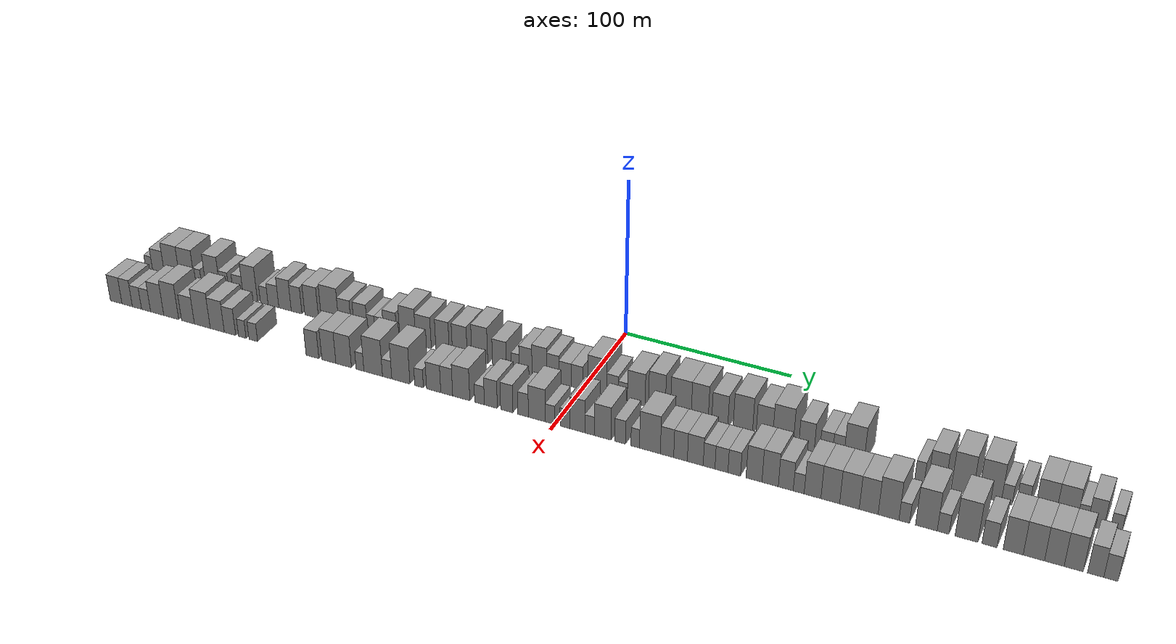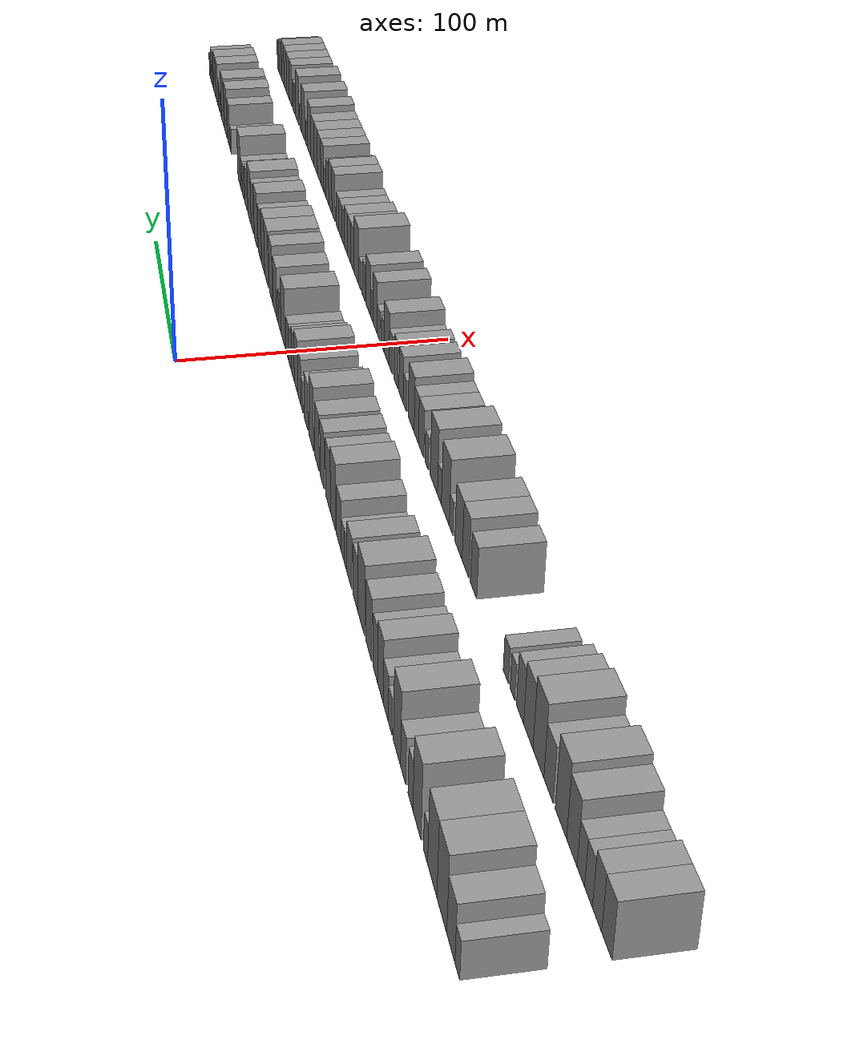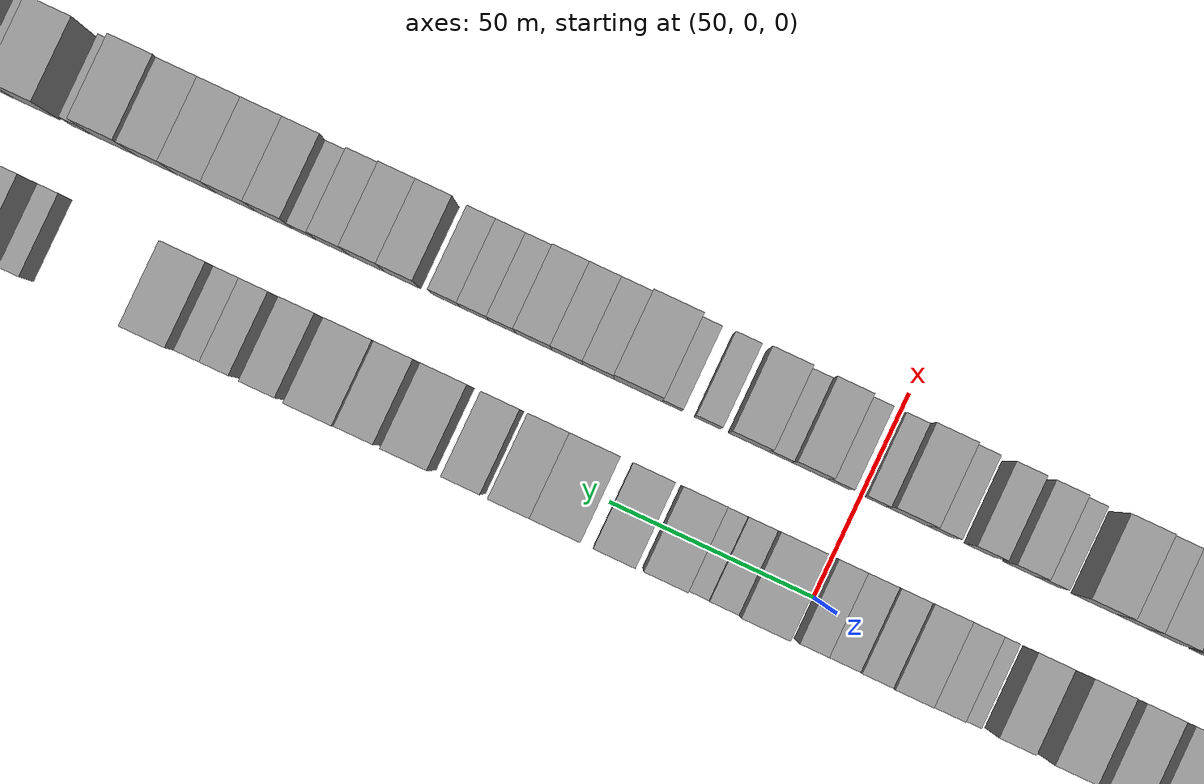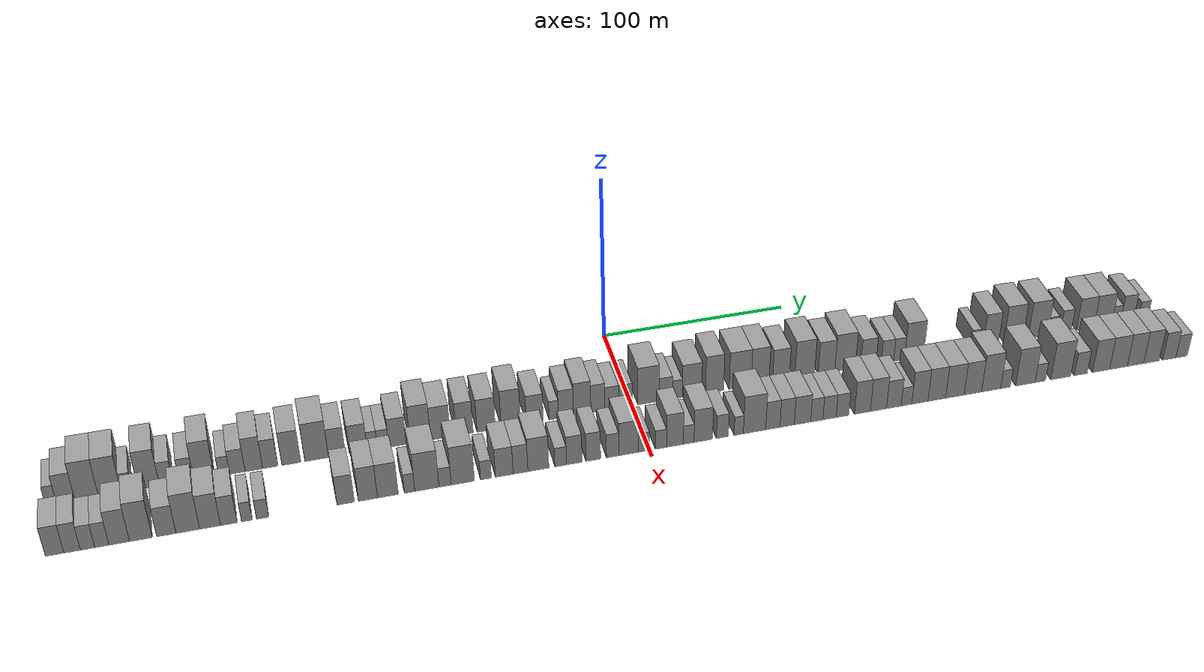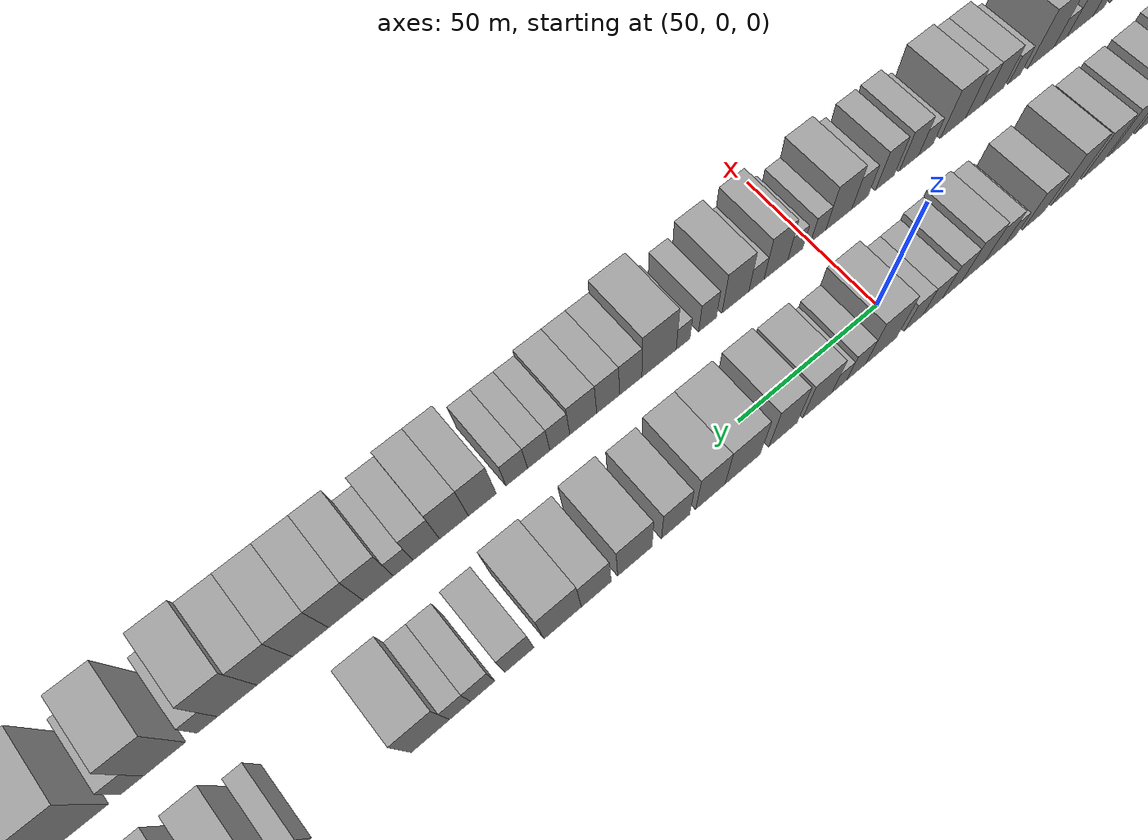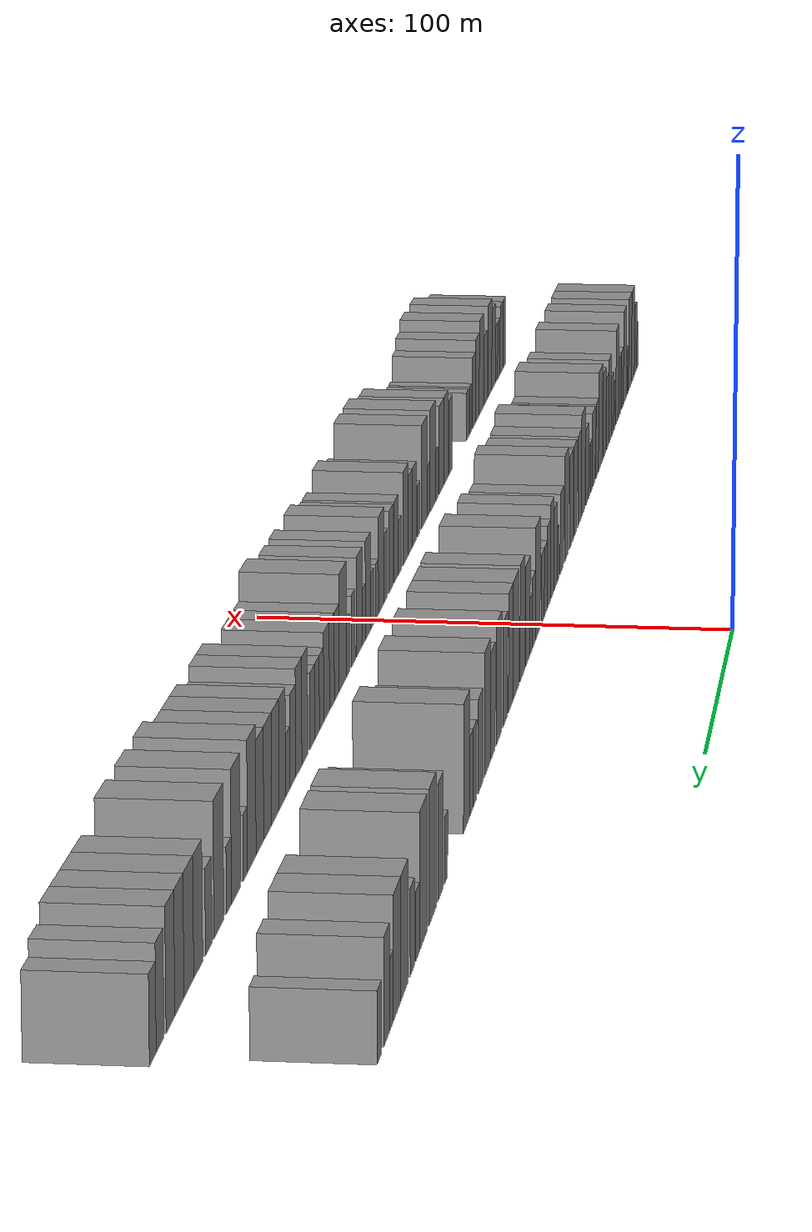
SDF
<sdf version="1.6">
 <world name="default">
  <scene>
   <sky><clouds><speed>12</speed></clouds></sky>
   <ambient>0.4 0.4 0.4 1</ambient>
   <background>0.7 0.7 0.7 1</background>
   <shadows>1</shadows>
  </scene>
  <gravity>0 0 -9.8066</gravity>
  <magnetic_field>6e-06 2.3e-05 -4.2e-05</magnetic_field>
  <physics default="0" name="default_physics" type="ode">
   <ode>
    <solver>
     <type>quick</type>
     <iters>10</iters>
     <sor>1.0</sor>
     <use_dynamic_moi_rescaling>0</use_dynamic_moi_rescaling>
    </solver>
    <constraints>
     <cfm>0</cfm>
     <erp>0.2</erp>
     <contact_max_correcting_vel>100</contact_max_correcting_vel>
     <contact_surface_layer>0.001</contact_surface_layer>
    </constraints>
   </ode>
   <max_step_size>0.004</max_step_size>
   <real_time_factor>1</real_time_factor>
   <real_time_update_rate>250</real_time_update_rate>
  </physics>
  <light name="sun" type="directional">
   <pose>0 0 10 0 0 0</pose>
   <diffuse>0.8 0.8 0.8 1</diffuse>
   <specular>0.2 0.2 0.2 1</specular>
   <attenuation>
    <range>1000</range>
    <constant>0.9</constant>
    <linear>0.01</linear>
    <quadratic>0.001</quadratic>
   </attenuation>
   <direction>-0.5 0.1 -0.9</direction>
  </light>
  <model name="building_1">
   <static>1</static>
   <pose>50.0000 -287.4973 0 0.000000 0.000000 0.000000</pose>
   <link name="link">
    <pose>0 0 6.00 0 0 0</pose>
    <collision name="collision"><geometry><box><size>20.0000 5.0055 12.0000</size></box></geometry></collision>
    <visual name="visual">
     <cast_shadows>0</cast_shadows>
     <geometry><box><size>20.0000 5.0055 12.0000</size></box></geometry>
     <material>
      <script>
       <uri>model://grey_wall/materials/scripts</uri>
       <uri>model://grey_wall/materials/textures</uri>
       <name>vrc/grey_wall</name>
      </script>
     </material>
    </visual>
   </link>
  </model>
  <model name="building_2">
   <static>1</static>
   <pose>50.0000 -280.6761 0 0.000000 0.000000 0.000000</pose>
   <link name="link">
    <pose>0 0 9.00 0 0 0</pose>
    <collision name="collision"><geometry><box><size>20.0000 8.6367 18.0000</size></box></geometry></collision>
    <visual name="visual">
     <cast_shadows>0</cast_shadows>
     <geometry><box><size>20.0000 8.6367 18.0000</size></box></geometry>
     <material>
      <script>
       <uri>model://grey_wall/materials/scripts</uri>
       <uri>model://grey_wall/materials/textures</uri>
       <name>vrc/grey_wall</name>
      </script>
     </material>
    </visual>
   </link>
  </model>
  <model name="building_3">
   <static>1</static>
   <pose>50.0000 -270.8673 0 0.000000 0.000000 0.000000</pose>
   <link name="link">
    <pose>0 0 12.00 0 0 0</pose>
    <collision name="collision"><geometry><box><size>20.0000 10.9810 24.0000</size></box></geometry></collision>
    <visual name="visual">
     <cast_shadows>0</cast_shadows>
     <geometry><box><size>20.0000 10.9810 24.0000</size></box></geometry>
     <material>
      <script>
       <uri>model://grey_wall/materials/scripts</uri>
       <uri>model://grey_wall/materials/textures</uri>
       <name>vrc/grey_wall</name>
      </script>
     </material>
    </visual>
   </link>
  </model>
  <model name="building_4">
   <static>1</static>
   <pose>50.0000 -259.9896 0 0.000000 0.000000 0.000000</pose>
   <link name="link">
    <pose>0 0 12.00 0 0 0</pose>
    <collision name="collision"><geometry><box><size>20.0000 10.7745 24.0000</size></box></geometry></collision>
    <visual name="visual">
     <cast_shadows>0</cast_shadows>
     <geometry><box><size>20.0000 10.7745 24.0000</size></box></geometry>
     <material>
      <script>
       <uri>model://grey_wall/materials/scripts</uri>
       <uri>model://grey_wall/materials/textures</uri>
       <name>vrc/grey_wall</name>
      </script>
     </material>
    </visual>
   </link>
  </model>
  <model name="building_5">
   <static>1</static>
   <pose>50.0000 -252.1168 0 0.000000 0.000000 0.000000</pose>
   <link name="link">
    <pose>0 0 6.00 0 0 0</pose>
    <collision name="collision"><geometry><box><size>20.0000 4.9711 12.0000</size></box></geometry></collision>
    <visual name="visual">
     <cast_shadows>0</cast_shadows>
     <geometry><box><size>20.0000 4.9711 12.0000</size></box></geometry>
     <material>
      <script>
       <uri>model://grey_wall/materials/scripts</uri>
       <uri>model://grey_wall/materials/textures</uri>
       <name>vrc/grey_wall</name>
      </script>
     </material>
    </visual>
   </link>
  </model>
  <model name="building_6">
   <static>1</static>
   <pose>50.0000 -241.5734 0 0.000000 0.000000 0.000000</pose>
   <link name="link">
    <pose>0 0 12.00 0 0 0</pose>
    <collision name="collision"><geometry><box><size>20.0000 10.1158 24.0000</size></box></geometry></collision>
    <visual name="visual">
     <cast_shadows>0</cast_shadows>
     <geometry><box><size>20.0000 10.1158 24.0000</size></box></geometry>
     <material>
      <script>
       <uri>model://grey_wall/materials/scripts</uri>
       <uri>model://grey_wall/materials/textures</uri>
       <name>vrc/grey_wall</name>
      </script>
     </material>
    </visual>
   </link>
  </model>
  <model name="building_7">
   <static>1</static>
   <pose>50.0000 -233.3102 0 0.000000 0.000000 0.000000</pose>
   <link name="link">
    <pose>0 0 7.50 0 0 0</pose>
    <collision name="collision"><geometry><box><size>20.0000 6.4105 15.0000</size></box></geometry></collision>
    <visual name="visual">
     <cast_shadows>0</cast_shadows>
     <geometry><box><size>20.0000 6.4105 15.0000</size></box></geometry>
     <material>
      <script>
       <uri>model://grey_wall/materials/scripts</uri>
       <uri>model://grey_wall/materials/textures</uri>
       <name>vrc/grey_wall</name>
      </script>
     </material>
    </visual>
   </link>
  </model>
  <model name="building_8">
   <static>1</static>
   <pose>50.0000 -223.6317 0 0.000000 0.000000 0.000000</pose>
   <link name="link">
    <pose>0 0 7.50 0 0 0</pose>
    <collision name="collision"><geometry><box><size>20.0000 6.9466 15.0000</size></box></geometry></collision>
    <visual name="visual">
     <cast_shadows>0</cast_shadows>
     <geometry><box><size>20.0000 6.9466 15.0000</size></box></geometry>
     <material>
      <script>
       <uri>model://grey_wall/materials/scripts</uri>
       <uri>model://grey_wall/materials/textures</uri>
       <name>vrc/grey_wall</name>
      </script>
     </material>
    </visual>
   </link>
  </model>
  <model name="building_9">
   <static>1</static>
   <pose>50.0000 -215.2181 0 0.000000 0.000000 0.000000</pose>
   <link name="link">
    <pose>0 0 12.00 0 0 0</pose>
    <collision name="collision"><geometry><box><size>20.0000 9.8805 24.0000</size></box></geometry></collision>
    <visual name="visual">
     <cast_shadows>0</cast_shadows>
     <geometry><box><size>20.0000 9.8805 24.0000</size></box></geometry>
     <material>
      <script>
       <uri>model://grey_wall/materials/scripts</uri>
       <uri>model://grey_wall/materials/textures</uri>
       <name>vrc/grey_wall</name>
      </script>
     </material>
    </visual>
   </link>
  </model>
  <model name="building_10">
   <static>1</static>
   <pose>50.0000 -205.6280 0 0.000000 0.000000 0.000000</pose>
   <link name="link">
    <pose>0 0 6.00 0 0 0</pose>
    <collision name="collision"><geometry><box><size>20.0000 5.2998 12.0000</size></box></geometry></collision>
    <visual name="visual">
     <cast_shadows>0</cast_shadows>
     <geometry><box><size>20.0000 5.2998 12.0000</size></box></geometry>
     <material>
      <script>
       <uri>model://grey_wall/materials/scripts</uri>
       <uri>model://grey_wall/materials/textures</uri>
       <name>vrc/grey_wall</name>
      </script>
     </material>
    </visual>
   </link>
  </model>
  <model name="building_11">
   <static>1</static>
   <pose>50.0000 -199.2638 0 0.000000 0.000000 0.000000</pose>
   <link name="link">
    <pose>0 0 7.50 0 0 0</pose>
    <collision name="collision"><geometry><box><size>20.0000 7.4287 15.0000</size></box></geometry></collision>
    <visual name="visual">
     <cast_shadows>0</cast_shadows>
     <geometry><box><size>20.0000 7.4287 15.0000</size></box></geometry>
     <material>
      <script>
       <uri>model://grey_wall/materials/scripts</uri>
       <uri>model://grey_wall/materials/textures</uri>
       <name>vrc/grey_wall</name>
      </script>
     </material>
    </visual>
   </link>
  </model>
  <model name="building_12">
   <static>1</static>
   <pose>50.0000 -191.2809 0 0.000000 0.000000 0.000000</pose>
   <link name="link">
    <pose>0 0 10.50 0 0 0</pose>
    <collision name="collision"><geometry><box><size>20.0000 8.5371 21.0000</size></box></geometry></collision>
    <visual name="visual">
     <cast_shadows>0</cast_shadows>
     <geometry><box><size>20.0000 8.5371 21.0000</size></box></geometry>
     <material>
      <script>
       <uri>model://grey_wall/materials/scripts</uri>
       <uri>model://grey_wall/materials/textures</uri>
       <name>vrc/grey_wall</name>
      </script>
     </material>
    </visual>
   </link>
  </model>
  <model name="building_13">
   <static>1</static>
   <pose>50.0000 -183.3547 0 0.000000 0.000000 0.000000</pose>
   <link name="link">
    <pose>0 0 9.00 0 0 0</pose>
    <collision name="collision"><geometry><box><size>20.0000 7.3152 18.0000</size></box></geometry></collision>
    <visual name="visual">
     <cast_shadows>0</cast_shadows>
     <geometry><box><size>20.0000 7.3152 18.0000</size></box></geometry>
     <material>
      <script>
       <uri>model://grey_wall/materials/scripts</uri>
       <uri>model://grey_wall/materials/textures</uri>
       <name>vrc/grey_wall</name>
      </script>
     </material>
    </visual>
   </link>
  </model>
  <model name="building_14">
   <static>1</static>
   <pose>50.0000 -173.0662 0 0.000000 0.000000 0.000000</pose>
   <link name="link">
    <pose>0 0 10.50 0 0 0</pose>
    <collision name="collision"><geometry><box><size>20.0000 9.2618 21.0000</size></box></geometry></collision>
    <visual name="visual">
     <cast_shadows>0</cast_shadows>
     <geometry><box><size>20.0000 9.2618 21.0000</size></box></geometry>
     <material>
      <script>
       <uri>model://grey_wall/materials/scripts</uri>
       <uri>model://grey_wall/materials/textures</uri>
       <name>vrc/grey_wall</name>
      </script>
     </material>
    </visual>
   </link>
  </model>
  <model name="building_15">
   <static>1</static>
   <pose>50.0000 -160.6138 0 0.000000 0.000000 0.000000</pose>
   <link name="link">
    <pose>0 0 12.00 0 0 0</pose>
    <collision name="collision"><geometry><box><size>20.0000 11.6430 24.0000</size></box></geometry></collision>
    <visual name="visual">
     <cast_shadows>0</cast_shadows>
     <geometry><box><size>20.0000 11.6430 24.0000</size></box></geometry>
     <material>
      <script>
       <uri>model://grey_wall/materials/scripts</uri>
       <uri>model://grey_wall/materials/textures</uri>
       <name>vrc/grey_wall</name>
      </script>
     </material>
    </visual>
   </link>
  </model>
  <model name="building_16">
   <static>1</static>
   <pose>50.0000 -150.6305 0 0.000000 0.000000 0.000000</pose>
   <link name="link">
    <pose>0 0 9.00 0 0 0</pose>
    <collision name="collision"><geometry><box><size>20.0000 8.3237 18.0000</size></box></geometry></collision>
    <visual name="visual">
     <cast_shadows>0</cast_shadows>
     <geometry><box><size>20.0000 8.3237 18.0000</size></box></geometry>
     <material>
      <script>
       <uri>model://grey_wall/materials/scripts</uri>
       <uri>model://grey_wall/materials/textures</uri>
       <name>vrc/grey_wall</name>
      </script>
     </material>
    </visual>
   </link>
  </model>
  <model name="building_17">
   <static>1</static>
   <pose>50.0000 -140.0535 0 0.000000 0.000000 0.000000</pose>
   <link name="link">
    <pose>0 0 9.00 0 0 0</pose>
    <collision name="collision"><geometry><box><size>20.0000 8.8303 18.0000</size></box></geometry></collision>
    <visual name="visual">
     <cast_shadows>0</cast_shadows>
     <geometry><box><size>20.0000 8.8303 18.0000</size></box></geometry>
     <material>
      <script>
       <uri>model://grey_wall/materials/scripts</uri>
       <uri>model://grey_wall/materials/textures</uri>
       <name>vrc/grey_wall</name>
      </script>
     </material>
    </visual>
   </link>
  </model>
  <model name="building_18">
   <static>1</static>
   <pose>50.0000 -133.1016 0 0.000000 0.000000 0.000000</pose>
   <link name="link">
    <pose>0 0 6.00 0 0 0</pose>
    <collision name="collision"><geometry><box><size>20.0000 5.0734 12.0000</size></box></geometry></collision>
    <visual name="visual">
     <cast_shadows>0</cast_shadows>
     <geometry><box><size>20.0000 5.0734 12.0000</size></box></geometry>
     <material>
      <script>
       <uri>model://grey_wall/materials/scripts</uri>
       <uri>model://grey_wall/materials/textures</uri>
       <name>vrc/grey_wall</name>
      </script>
     </material>
    </visual>
   </link>
  </model>
  <model name="building_19">
   <static>1</static>
   <pose>50.0000 -127.7037 0 0.000000 0.000000 0.000000</pose>
   <link name="link">
    <pose>0 0 6.00 0 0 0</pose>
    <collision name="collision"><geometry><box><size>20.0000 5.7223 12.0000</size></box></geometry></collision>
    <visual name="visual">
     <cast_shadows>0</cast_shadows>
     <geometry><box><size>20.0000 5.7223 12.0000</size></box></geometry>
     <material>
      <script>
       <uri>model://grey_wall/materials/scripts</uri>
       <uri>model://grey_wall/materials/textures</uri>
       <name>vrc/grey_wall</name>
      </script>
     </material>
    </visual>
   </link>
  </model>
  <model name="building_20">
   <static>1</static>
   <pose>50.0000 -120.5099 0 0.000000 0.000000 0.000000</pose>
   <link name="link">
    <pose>0 0 9.00 0 0 0</pose>
    <collision name="collision"><geometry><box><size>20.0000 8.6654 18.0000</size></box></geometry></collision>
    <visual name="visual">
     <cast_shadows>0</cast_shadows>
     <geometry><box><size>20.0000 8.6654 18.0000</size></box></geometry>
     <material>
      <script>
       <uri>model://grey_wall/materials/scripts</uri>
       <uri>model://grey_wall/materials/textures</uri>
       <name>vrc/grey_wall</name>
      </script>
     </material>
    </visual>
   </link>
  </model>
  <model name="building_21">
   <static>1</static>
   <pose>50.0000 -109.0209 0 0.000000 0.000000 0.000000</pose>
   <link name="link">
    <pose>0 0 12.00 0 0 0</pose>
    <collision name="collision"><geometry><box><size>20.0000 10.3126 24.0000</size></box></geometry></collision>
    <visual name="visual">
     <cast_shadows>0</cast_shadows>
     <geometry><box><size>20.0000 10.3126 24.0000</size></box></geometry>
     <material>
      <script>
       <uri>model://grey_wall/materials/scripts</uri>
       <uri>model://grey_wall/materials/textures</uri>
       <name>vrc/grey_wall</name>
      </script>
     </material>
    </visual>
   </link>
  </model>
  <model name="building_22">
   <static>1</static>
   <pose>50.0000 -98.8881 0 0.000000 0.000000 0.000000</pose>
   <link name="link">
    <pose>0 0 10.50 0 0 0</pose>
    <collision name="collision"><geometry><box><size>20.0000 9.9530 21.0000</size></box></geometry></collision>
    <visual name="visual">
     <cast_shadows>0</cast_shadows>
     <geometry><box><size>20.0000 9.9530 21.0000</size></box></geometry>
     <material>
      <script>
       <uri>model://grey_wall/materials/scripts</uri>
       <uri>model://grey_wall/materials/textures</uri>
       <name>vrc/grey_wall</name>
      </script>
     </material>
    </visual>
   </link>
  </model>
  <model name="building_23">
   <static>1</static>
   <pose>50.0000 -86.6172 0 0.000000 0.000000 0.000000</pose>
   <link name="link">
    <pose>0 0 10.50 0 0 0</pose>
    <collision name="collision"><geometry><box><size>20.0000 8.5887 21.0000</size></box></geometry></collision>
    <visual name="visual">
     <cast_shadows>0</cast_shadows>
     <geometry><box><size>20.0000 8.5887 21.0000</size></box></geometry>
     <material>
      <script>
       <uri>model://grey_wall/materials/scripts</uri>
       <uri>model://grey_wall/materials/textures</uri>
       <name>vrc/grey_wall</name>
      </script>
     </material>
    </visual>
   </link>
  </model>
  <model name="building_24">
   <static>1</static>
   <pose>50.0000 -75.6412 0 0.000000 0.000000 0.000000</pose>
   <link name="link">
    <pose>0 0 10.50 0 0 0</pose>
    <collision name="collision"><geometry><box><size>20.0000 9.3633 21.0000</size></box></geometry></collision>
    <visual name="visual">
     <cast_shadows>0</cast_shadows>
     <geometry><box><size>20.0000 9.3633 21.0000</size></box></geometry>
     <material>
      <script>
       <uri>model://grey_wall/materials/scripts</uri>
       <uri>model://grey_wall/materials/textures</uri>
       <name>vrc/grey_wall</name>
      </script>
     </material>
    </visual>
   </link>
  </model>
  <model name="building_25">
   <static>1</static>
   <pose>50.0000 -62.9925 0 0.000000 0.000000 0.000000</pose>
   <link name="link">
    <pose>0 0 12.00 0 0 0</pose>
    <collision name="collision"><geometry><box><size>20.0000 9.9341 24.0000</size></box></geometry></collision>
    <visual name="visual">
     <cast_shadows>0</cast_shadows>
     <geometry><box><size>20.0000 9.9341 24.0000</size></box></geometry>
     <material>
      <script>
       <uri>model://grey_wall/materials/scripts</uri>
       <uri>model://grey_wall/materials/textures</uri>
       <name>vrc/grey_wall</name>
      </script>
     </material>
    </visual>
   </link>
  </model>
  <model name="building_26">
   <static>1</static>
   <pose>50.0000 -50.6560 0 0.000000 0.000000 0.000000</pose>
   <link name="link">
    <pose>0 0 9.00 0 0 0</pose>
    <collision name="collision"><geometry><box><size>20.0000 8.7389 18.0000</size></box></geometry></collision>
    <visual name="visual">
     <cast_shadows>0</cast_shadows>
     <geometry><box><size>20.0000 8.7389 18.0000</size></box></geometry>
     <material>
      <script>
       <uri>model://grey_wall/materials/scripts</uri>
       <uri>model://grey_wall/materials/textures</uri>
       <name>vrc/grey_wall</name>
      </script>
     </material>
    </visual>
   </link>
  </model>
  <model name="building_27">
   <static>1</static>
   <pose>50.0000 -40.8635 0 0.000000 0.000000 0.000000</pose>
   <link name="link">
    <pose>0 0 6.00 0 0 0</pose>
    <collision name="collision"><geometry><box><size>20.0000 4.8460 12.0000</size></box></geometry></collision>
    <visual name="visual">
     <cast_shadows>0</cast_shadows>
     <geometry><box><size>20.0000 4.8460 12.0000</size></box></geometry>
     <material>
      <script>
       <uri>model://grey_wall/materials/scripts</uri>
       <uri>model://grey_wall/materials/textures</uri>
       <name>vrc/grey_wall</name>
      </script>
     </material>
    </visual>
   </link>
  </model>
  <model name="building_28">
   <static>1</static>
   <pose>50.0000 -34.4788 0 0.000000 0.000000 0.000000</pose>
   <link name="link">
    <pose>0 0 9.00 0 0 0</pose>
    <collision name="collision"><geometry><box><size>20.0000 7.9235 18.0000</size></box></geometry></collision>
    <visual name="visual">
     <cast_shadows>0</cast_shadows>
     <geometry><box><size>20.0000 7.9235 18.0000</size></box></geometry>
     <material>
      <script>
       <uri>model://grey_wall/materials/scripts</uri>
       <uri>model://grey_wall/materials/textures</uri>
       <name>vrc/grey_wall</name>
      </script>
     </material>
    </visual>
   </link>
  </model>
  <model name="building_29">
   <static>1</static>
   <pose>50.0000 -26.0152 0 0.000000 0.000000 0.000000</pose>
   <link name="link">
    <pose>0 0 10.50 0 0 0</pose>
    <collision name="collision"><geometry><box><size>20.0000 9.0037 21.0000</size></box></geometry></collision>
    <visual name="visual">
     <cast_shadows>0</cast_shadows>
     <geometry><box><size>20.0000 9.0037 21.0000</size></box></geometry>
     <material>
      <script>
       <uri>model://grey_wall/materials/scripts</uri>
       <uri>model://grey_wall/materials/textures</uri>
       <name>vrc/grey_wall</name>
      </script>
     </material>
    </visual>
   </link>
  </model>
  <model name="building_30">
   <static>1</static>
   <pose>50.0000 -17.8547 0 0.000000 0.000000 0.000000</pose>
   <link name="link">
    <pose>0 0 9.00 0 0 0</pose>
    <collision name="collision"><geometry><box><size>20.0000 7.3173 18.0000</size></box></geometry></collision>
    <visual name="visual">
     <cast_shadows>0</cast_shadows>
     <geometry><box><size>20.0000 7.3173 18.0000</size></box></geometry>
     <material>
      <script>
       <uri>model://grey_wall/materials/scripts</uri>
       <uri>model://grey_wall/materials/textures</uri>
       <name>vrc/grey_wall</name>
      </script>
     </material>
    </visual>
   </link>
  </model>
  <model name="building_31">
   <static>1</static>
   <pose>50.0000 -10.4761 0 0.000000 0.000000 0.000000</pose>
   <link name="link">
    <pose>0 0 7.50 0 0 0</pose>
    <collision name="collision"><geometry><box><size>20.0000 7.4399 15.0000</size></box></geometry></collision>
    <visual name="visual">
     <cast_shadows>0</cast_shadows>
     <geometry><box><size>20.0000 7.4399 15.0000</size></box></geometry>
     <material>
      <script>
       <uri>model://grey_wall/materials/scripts</uri>
       <uri>model://grey_wall/materials/textures</uri>
       <name>vrc/grey_wall</name>
      </script>
     </material>
    </visual>
   </link>
  </model>
  <model name="building_32">
   <static>1</static>
   <pose>50.0000 -3.2750 0 0.000000 0.000000 0.000000</pose>
   <link name="link">
    <pose>0 0 7.50 0 0 0</pose>
    <collision name="collision"><geometry><box><size>20.0000 6.9623 15.0000</size></box></geometry></collision>
    <visual name="visual">
     <cast_shadows>0</cast_shadows>
     <geometry><box><size>20.0000 6.9623 15.0000</size></box></geometry>
     <material>
      <script>
       <uri>model://grey_wall/materials/scripts</uri>
       <uri>model://grey_wall/materials/textures</uri>
       <name>vrc/grey_wall</name>
      </script>
     </material>
    </visual>
   </link>
  </model>
  <model name="building_33">
   <static>1</static>
   <pose>50.0000 8.9000 0 0.000000 0.000000 0.000000</pose>
   <link name="link">
    <pose>0 0 12.00 0 0 0</pose>
    <collision name="collision"><geometry><box><size>20.0000 11.3878 24.0000</size></box></geometry></collision>
    <visual name="visual">
     <cast_shadows>0</cast_shadows>
     <geometry><box><size>20.0000 11.3878 24.0000</size></box></geometry>
     <material>
      <script>
       <uri>model://grey_wall/materials/scripts</uri>
       <uri>model://grey_wall/materials/textures</uri>
       <name>vrc/grey_wall</name>
      </script>
     </material>
    </visual>
   </link>
  </model>
  <model name="building_34">
   <static>1</static>
   <pose>50.0000 18.0615 0 0.000000 0.000000 0.000000</pose>
   <link name="link">
    <pose>0 0 7.50 0 0 0</pose>
    <collision name="collision"><geometry><box><size>20.0000 6.9351 15.0000</size></box></geometry></collision>
    <visual name="visual">
     <cast_shadows>0</cast_shadows>
     <geometry><box><size>20.0000 6.9351 15.0000</size></box></geometry>
     <material>
      <script>
       <uri>model://grey_wall/materials/scripts</uri>
       <uri>model://grey_wall/materials/textures</uri>
       <name>vrc/grey_wall</name>
      </script>
     </material>
    </visual>
   </link>
  </model>
  <model name="building_35">
   <static>1</static>
   <pose>50.0000 24.1710 0 0.000000 0.000000 0.000000</pose>
   <link name="link">
    <pose>0 0 6.00 0 0 0</pose>
    <collision name="collision"><geometry><box><size>20.0000 5.2841 12.0000</size></box></geometry></collision>
    <visual name="visual">
     <cast_shadows>0</cast_shadows>
     <geometry><box><size>20.0000 5.2841 12.0000</size></box></geometry>
     <material>
      <script>
       <uri>model://grey_wall/materials/scripts</uri>
       <uri>model://grey_wall/materials/textures</uri>
       <name>vrc/grey_wall</name>
      </script>
     </material>
    </visual>
   </link>
  </model>
  <model name="building_36">
   <static>1</static>
   <pose>50.0000 32.0072 0 0.000000 0.000000 0.000000</pose>
   <link name="link">
    <pose>0 0 10.50 0 0 0</pose>
    <collision name="collision"><geometry><box><size>20.0000 10.3882 21.0000</size></box></geometry></collision>
    <visual name="visual">
     <cast_shadows>0</cast_shadows>
     <geometry><box><size>20.0000 10.3882 21.0000</size></box></geometry>
     <material>
      <script>
       <uri>model://grey_wall/materials/scripts</uri>
       <uri>model://grey_wall/materials/textures</uri>
       <name>vrc/grey_wall</name>
      </script>
     </material>
    </visual>
   </link>
  </model>
  <model name="building_37">
   <static>1</static>
   <pose>50.0000 44.0992 0 0.000000 0.000000 0.000000</pose>
   <link name="link">
    <pose>0 0 12.00 0 0 0</pose>
    <collision name="collision"><geometry><box><size>20.0000 9.7959 24.0000</size></box></geometry></collision>
    <visual name="visual">
     <cast_shadows>0</cast_shadows>
     <geometry><box><size>20.0000 9.7959 24.0000</size></box></geometry>
     <material>
      <script>
       <uri>model://grey_wall/materials/scripts</uri>
       <uri>model://grey_wall/materials/textures</uri>
       <name>vrc/grey_wall</name>
      </script>
     </material>
    </visual>
   </link>
  </model>
  <model name="building_38">
   <static>1</static>
   <pose>50.0000 57.9463 0 0.000000 0.000000 0.000000</pose>
   <link name="link">
    <pose>0 0 12.00 0 0 0</pose>
    <collision name="collision"><geometry><box><size>20.0000 11.8983 24.0000</size></box></geometry></collision>
    <visual name="visual">
     <cast_shadows>0</cast_shadows>
     <geometry><box><size>20.0000 11.8983 24.0000</size></box></geometry>
     <material>
      <script>
       <uri>model://grey_wall/materials/scripts</uri>
       <uri>model://grey_wall/materials/textures</uri>
       <name>vrc/grey_wall</name>
      </script>
     </material>
    </visual>
   </link>
  </model>
  <model name="building_39">
   <static>1</static>
   <pose>50.0000 68.7560 0 0.000000 0.000000 0.000000</pose>
   <link name="link">
    <pose>0 0 12.00 0 0 0</pose>
    <collision name="collision"><geometry><box><size>20.0000 9.7211 24.0000</size></box></geometry></collision>
    <visual name="visual">
     <cast_shadows>0</cast_shadows>
     <geometry><box><size>20.0000 9.7211 24.0000</size></box></geometry>
     <material>
      <script>
       <uri>model://grey_wall/materials/scripts</uri>
       <uri>model://grey_wall/materials/textures</uri>
       <name>vrc/grey_wall</name>
      </script>
     </material>
    </visual>
   </link>
  </model>
  <model name="building_40">
   <static>1</static>
   <pose>50.0000 80.1845 0 0.000000 0.000000 0.000000</pose>
   <link name="link">
    <pose>0 0 10.50 0 0 0</pose>
    <collision name="collision"><geometry><box><size>20.0000 9.1358 21.0000</size></box></geometry></collision>
    <visual name="visual">
     <cast_shadows>0</cast_shadows>
     <geometry><box><size>20.0000 9.1358 21.0000</size></box></geometry>
     <material>
      <script>
       <uri>model://grey_wall/materials/scripts</uri>
       <uri>model://grey_wall/materials/textures</uri>
       <name>vrc/grey_wall</name>
      </script>
     </material>
    </visual>
   </link>
  </model>
  <model name="building_41">
   <static>1</static>
   <pose>50.0000 93.1958 0 0.000000 0.000000 0.000000</pose>
   <link name="link">
    <pose>0 0 12.00 0 0 0</pose>
    <collision name="collision"><geometry><box><size>20.0000 10.8868 24.0000</size></box></geometry></collision>
    <visual name="visual">
     <cast_shadows>0</cast_shadows>
     <geometry><box><size>20.0000 10.8868 24.0000</size></box></geometry>
     <material>
      <script>
       <uri>model://grey_wall/materials/scripts</uri>
       <uri>model://grey_wall/materials/textures</uri>
       <name>vrc/grey_wall</name>
      </script>
     </material>
    </visual>
   </link>
  </model>
  <model name="building_42">
   <static>1</static>
   <pose>50.0000 105.2544 0 0.000000 0.000000 0.000000</pose>
   <link name="link">
    <pose>0 0 10.50 0 0 0</pose>
    <collision name="collision"><geometry><box><size>20.0000 9.2304 21.0000</size></box></geometry></collision>
    <visual name="visual">
     <cast_shadows>0</cast_shadows>
     <geometry><box><size>20.0000 9.2304 21.0000</size></box></geometry>
     <material>
      <script>
       <uri>model://grey_wall/materials/scripts</uri>
       <uri>model://grey_wall/materials/textures</uri>
       <name>vrc/grey_wall</name>
      </script>
     </material>
    </visual>
   </link>
  </model>
  <model name="building_43">
   <static>1</static>
   <pose>50.0000 115.5424 0 0.000000 0.000000 0.000000</pose>
   <link name="link">
    <pose>0 0 12.00 0 0 0</pose>
    <collision name="collision"><geometry><box><size>20.0000 11.3457 24.0000</size></box></geometry></collision>
    <visual name="visual">
     <cast_shadows>0</cast_shadows>
     <geometry><box><size>20.0000 11.3457 24.0000</size></box></geometry>
     <material>
      <script>
       <uri>model://grey_wall/materials/scripts</uri>
       <uri>model://grey_wall/materials/textures</uri>
       <name>vrc/grey_wall</name>
      </script>
     </material>
    </visual>
   </link>
  </model>
  <model name="building_44">
   <static>1</static>
   <pose>50.0000 128.4748 0 0.000000 0.000000 0.000000</pose>
   <link name="link">
    <pose>0 0 9.00 0 0 0</pose>
    <collision name="collision"><geometry><box><size>20.0000 8.5190 18.0000</size></box></geometry></collision>
    <visual name="visual">
     <cast_shadows>0</cast_shadows>
     <geometry><box><size>20.0000 8.5190 18.0000</size></box></geometry>
     <material>
      <script>
       <uri>model://grey_wall/materials/scripts</uri>
       <uri>model://grey_wall/materials/textures</uri>
       <name>vrc/grey_wall</name>
      </script>
     </material>
    </visual>
   </link>
  </model>
  <model name="building_45">
   <static>1</static>
   <pose>50.0000 139.2101 0 0.000000 0.000000 0.000000</pose>
   <link name="link">
    <pose>0 0 7.50 0 0 0</pose>
    <collision name="collision"><geometry><box><size>20.0000 6.9514 15.0000</size></box></geometry></collision>
    <visual name="visual">
     <cast_shadows>0</cast_shadows>
     <geometry><box><size>20.0000 6.9514 15.0000</size></box></geometry>
     <material>
      <script>
       <uri>model://grey_wall/materials/scripts</uri>
       <uri>model://grey_wall/materials/textures</uri>
       <name>vrc/grey_wall</name>
      </script>
     </material>
    </visual>
   </link>
  </model>
  <model name="building_46">
   <static>1</static>
   <pose>50.0000 145.6964 0 0.000000 0.000000 0.000000</pose>
   <link name="link">
    <pose>0 0 7.50 0 0 0</pose>
    <collision name="collision"><geometry><box><size>20.0000 6.0213 15.0000</size></box></geometry></collision>
    <visual name="visual">
     <cast_shadows>0</cast_shadows>
     <geometry><box><size>20.0000 6.0213 15.0000</size></box></geometry>
     <material>
      <script>
       <uri>model://grey_wall/materials/scripts</uri>
       <uri>model://grey_wall/materials/textures</uri>
       <name>vrc/grey_wall</name>
      </script>
     </material>
    </visual>
   </link>
  </model>
  <model name="building_47">
   <static>1</static>
   <pose>50.0000 154.1085 0 0.000000 0.000000 0.000000</pose>
   <link name="link">
    <pose>0 0 12.00 0 0 0</pose>
    <collision name="collision"><geometry><box><size>20.0000 10.8028 24.0000</size></box></geometry></collision>
    <visual name="visual">
     <cast_shadows>0</cast_shadows>
     <geometry><box><size>20.0000 10.8028 24.0000</size></box></geometry>
     <material>
      <script>
       <uri>model://grey_wall/materials/scripts</uri>
       <uri>model://grey_wall/materials/textures</uri>
       <name>vrc/grey_wall</name>
      </script>
     </material>
    </visual>
   </link>
  </model>
  <model name="building_48">
   <static>1</static>
   <pose>50.0000 189.0188 0 0.000000 0.000000 0.000000</pose>
   <link name="link">
    <pose>0 0 6.00 0 0 0</pose>
    <collision name="collision"><geometry><box><size>20.0000 5.0059 12.0000</size></box></geometry></collision>
    <visual name="visual">
     <cast_shadows>0</cast_shadows>
     <geometry><box><size>20.0000 5.0059 12.0000</size></box></geometry>
     <material>
      <script>
       <uri>model://grey_wall/materials/scripts</uri>
       <uri>model://grey_wall/materials/textures</uri>
       <name>vrc/grey_wall</name>
      </script>
     </material>
    </visual>
   </link>
  </model>
  <model name="building_49">
   <static>1</static>
   <pose>50.0000 197.9715 0 0.000000 0.000000 0.000000</pose>
   <link name="link">
    <pose>0 0 10.50 0 0 0</pose>
    <collision name="collision"><geometry><box><size>20.0000 8.8994 21.0000</size></box></geometry></collision>
    <visual name="visual">
     <cast_shadows>0</cast_shadows>
     <geometry><box><size>20.0000 8.8994 21.0000</size></box></geometry>
     <material>
      <script>
       <uri>model://grey_wall/materials/scripts</uri>
       <uri>model://grey_wall/materials/textures</uri>
       <name>vrc/grey_wall</name>
      </script>
     </material>
    </visual>
   </link>
  </model>
  <model name="building_50">
   <static>1</static>
   <pose>50.0000 210.9575 0 0.000000 0.000000 0.000000</pose>
   <link name="link">
    <pose>0 0 12.00 0 0 0</pose>
    <collision name="collision"><geometry><box><size>20.0000 11.0726 24.0000</size></box></geometry></collision>
    <visual name="visual">
     <cast_shadows>0</cast_shadows>
     <geometry><box><size>20.0000 11.0726 24.0000</size></box></geometry>
     <material>
      <script>
       <uri>model://grey_wall/materials/scripts</uri>
       <uri>model://grey_wall/materials/textures</uri>
       <name>vrc/grey_wall</name>
      </script>
     </material>
    </visual>
   </link>
  </model>
  <model name="building_51">
   <static>1</static>
   <pose>50.0000 225.2225 0 0.000000 0.000000 0.000000</pose>
   <link name="link">
    <pose>0 0 12.00 0 0 0</pose>
    <collision name="collision"><geometry><box><size>20.0000 11.4574 24.0000</size></box></geometry></collision>
    <visual name="visual">
     <cast_shadows>0</cast_shadows>
     <geometry><box><size>20.0000 11.4574 24.0000</size></box></geometry>
     <material>
      <script>
       <uri>model://grey_wall/materials/scripts</uri>
       <uri>model://grey_wall/materials/textures</uri>
       <name>vrc/grey_wall</name>
      </script>
     </material>
    </visual>
   </link>
  </model>
  <model name="building_52">
   <static>1</static>
   <pose>50.0000 233.6686 0 0.000000 0.000000 0.000000</pose>
   <link name="link">
    <pose>0 0 6.00 0 0 0</pose>
    <collision name="collision"><geometry><box><size>20.0000 5.4349 12.0000</size></box></geometry></collision>
    <visual name="visual">
     <cast_shadows>0</cast_shadows>
     <geometry><box><size>20.0000 5.4349 12.0000</size></box></geometry>
     <material>
      <script>
       <uri>model://grey_wall/materials/scripts</uri>
       <uri>model://grey_wall/materials/textures</uri>
       <name>vrc/grey_wall</name>
      </script>
     </material>
    </visual>
   </link>
  </model>
  <model name="building_53">
   <static>1</static>
   <pose>50.0000 241.5893 0 0.000000 0.000000 0.000000</pose>
   <link name="link">
    <pose>0 0 7.50 0 0 0</pose>
    <collision name="collision"><geometry><box><size>20.0000 6.4063 15.0000</size></box></geometry></collision>
    <visual name="visual">
     <cast_shadows>0</cast_shadows>
     <geometry><box><size>20.0000 6.4063 15.0000</size></box></geometry>
     <material>
      <script>
       <uri>model://grey_wall/materials/scripts</uri>
       <uri>model://grey_wall/materials/textures</uri>
       <name>vrc/grey_wall</name>
      </script>
     </material>
    </visual>
   </link>
  </model>
  <model name="building_54">
   <static>1</static>
   <pose>50.0000 252.9674 0 0.000000 0.000000 0.000000</pose>
   <link name="link">
    <pose>0 0 10.50 0 0 0</pose>
    <collision name="collision"><geometry><box><size>20.0000 10.3499 21.0000</size></box></geometry></collision>
    <visual name="visual">
     <cast_shadows>0</cast_shadows>
     <geometry><box><size>20.0000 10.3499 21.0000</size></box></geometry>
     <material>
      <script>
       <uri>model://grey_wall/materials/scripts</uri>
       <uri>model://grey_wall/materials/textures</uri>
       <name>vrc/grey_wall</name>
      </script>
     </material>
    </visual>
   </link>
  </model>
  <model name="building_55">
   <static>1</static>
   <pose>50.0000 263.3707 0 0.000000 0.000000 0.000000</pose>
   <link name="link">
    <pose>0 0 10.50 0 0 0</pose>
    <collision name="collision"><geometry><box><size>20.0000 10.4568 21.0000</size></box></geometry></collision>
    <visual name="visual">
     <cast_shadows>0</cast_shadows>
     <geometry><box><size>20.0000 10.4568 21.0000</size></box></geometry>
     <material>
      <script>
       <uri>model://grey_wall/materials/scripts</uri>
       <uri>model://grey_wall/materials/textures</uri>
       <name>vrc/grey_wall</name>
      </script>
     </material>
    </visual>
   </link>
  </model>
  <model name="building_56">
   <static>1</static>
   <pose>50.0000 271.1727 0 0.000000 0.000000 0.000000</pose>
   <link name="link">
    <pose>0 0 6.00 0 0 0</pose>
    <collision name="collision"><geometry><box><size>20.0000 5.1471 12.0000</size></box></geometry></collision>
    <visual name="visual">
     <cast_shadows>0</cast_shadows>
     <geometry><box><size>20.0000 5.1471 12.0000</size></box></geometry>
     <material>
      <script>
       <uri>model://grey_wall/materials/scripts</uri>
       <uri>model://grey_wall/materials/textures</uri>
       <name>vrc/grey_wall</name>
      </script>
     </material>
    </visual>
   </link>
  </model>
  <model name="building_57">
   <static>1</static>
   <pose>50.0000 277.6704 0 0.000000 0.000000 0.000000</pose>
   <link name="link">
    <pose>0 0 9.00 0 0 0</pose>
    <collision name="collision"><geometry><box><size>20.0000 7.8482 18.0000</size></box></geometry></collision>
    <visual name="visual">
     <cast_shadows>0</cast_shadows>
     <geometry><box><size>20.0000 7.8482 18.0000</size></box></geometry>
     <material>
      <script>
       <uri>model://grey_wall/materials/scripts</uri>
       <uri>model://grey_wall/materials/textures</uri>
       <name>vrc/grey_wall</name>
      </script>
     </material>
    </visual>
   </link>
  </model>
  <model name="building_58">
   <static>1</static>
   <pose>50.0000 287.4004 0 0.000000 0.000000 0.000000</pose>
   <link name="link">
    <pose>0 0 6.00 0 0 0</pose>
    <collision name="collision"><geometry><box><size>20.0000 5.6119 12.0000</size></box></geometry></collision>
    <visual name="visual">
     <cast_shadows>0</cast_shadows>
     <geometry><box><size>20.0000 5.6119 12.0000</size></box></geometry>
     <material>
      <script>
       <uri>model://grey_wall/materials/scripts</uri>
       <uri>model://grey_wall/materials/textures</uri>
       <name>vrc/grey_wall</name>
      </script>
     </material>
    </visual>
   </link>
  </model>
  <model name="building_59">
   <static>1</static>
   <pose>85.0000 -285.8442 0 0.000000 0.000000 0.000000</pose>
   <link name="link">
    <pose>0 0 9.00 0 0 0</pose>
    <collision name="collision"><geometry><box><size>20.0000 8.3116 18.0000</size></box></geometry></collision>
    <visual name="visual">
     <cast_shadows>0</cast_shadows>
     <geometry><box><size>20.0000 8.3116 18.0000</size></box></geometry>
     <material>
      <script>
       <uri>model://grey_wall/materials/scripts</uri>
       <uri>model://grey_wall/materials/textures</uri>
       <name>vrc/grey_wall</name>
      </script>
     </material>
    </visual>
   </link>
  </model>
  <model name="building_60">
   <static>1</static>
   <pose>85.0000 -277.9580 0 0.000000 0.000000 0.000000</pose>
   <link name="link">
    <pose>0 0 9.00 0 0 0</pose>
    <collision name="collision"><geometry><box><size>20.0000 7.4609 18.0000</size></box></geometry></collision>
    <visual name="visual">
     <cast_shadows>0</cast_shadows>
     <geometry><box><size>20.0000 7.4609 18.0000</size></box></geometry>
     <material>
      <script>
       <uri>model://grey_wall/materials/scripts</uri>
       <uri>model://grey_wall/materials/textures</uri>
       <name>vrc/grey_wall</name>
      </script>
     </material>
    </visual>
   </link>
  </model>
  <model name="building_61">
   <static>1</static>
   <pose>85.0000 -270.9569 0 0.000000 0.000000 0.000000</pose>
   <link name="link">
    <pose>0 0 7.50 0 0 0</pose>
    <collision name="collision"><geometry><box><size>20.0000 6.5413 15.0000</size></box></geometry></collision>
    <visual name="visual">
     <cast_shadows>0</cast_shadows>
     <geometry><box><size>20.0000 6.5413 15.0000</size></box></geometry>
     <material>
      <script>
       <uri>model://grey_wall/materials/scripts</uri>
       <uri>model://grey_wall/materials/textures</uri>
       <name>vrc/grey_wall</name>
      </script>
     </material>
    </visual>
   </link>
  </model>
  <model name="building_62">
   <static>1</static>
   <pose>85.0000 -264.4791 0 0.000000 0.000000 0.000000</pose>
   <link name="link">
    <pose>0 0 7.50 0 0 0</pose>
    <collision name="collision"><geometry><box><size>20.0000 6.4141 15.0000</size></box></geometry></collision>
    <visual name="visual">
     <cast_shadows>0</cast_shadows>
     <geometry><box><size>20.0000 6.4141 15.0000</size></box></geometry>
     <material>
      <script>
       <uri>model://grey_wall/materials/scripts</uri>
       <uri>model://grey_wall/materials/textures</uri>
       <name>vrc/grey_wall</name>
      </script>
     </material>
    </visual>
   </link>
  </model>
  <model name="building_63">
   <static>1</static>
   <pose>85.0000 -256.6060 0 0.000000 0.000000 0.000000</pose>
   <link name="link">
    <pose>0 0 10.50 0 0 0</pose>
    <collision name="collision"><geometry><box><size>20.0000 9.3320 21.0000</size></box></geometry></collision>
    <visual name="visual">
     <cast_shadows>0</cast_shadows>
     <geometry><box><size>20.0000 9.3320 21.0000</size></box></geometry>
     <material>
      <script>
       <uri>model://grey_wall/materials/scripts</uri>
       <uri>model://grey_wall/materials/textures</uri>
       <name>vrc/grey_wall</name>
      </script>
     </material>
    </visual>
   </link>
  </model>
  <model name="building_64">
   <static>1</static>
   <pose>85.0000 -246.7044 0 0.000000 0.000000 0.000000</pose>
   <link name="link">
    <pose>0 0 12.00 0 0 0</pose>
    <collision name="collision"><geometry><box><size>20.0000 10.4712 24.0000</size></box></geometry></collision>
    <visual name="visual">
     <cast_shadows>0</cast_shadows>
     <geometry><box><size>20.0000 10.4712 24.0000</size></box></geometry>
     <material>
      <script>
       <uri>model://grey_wall/materials/scripts</uri>
       <uri>model://grey_wall/materials/textures</uri>
       <name>vrc/grey_wall</name>
      </script>
     </material>
    </visual>
   </link>
  </model>
  <model name="building_65">
   <static>1</static>
   <pose>85.0000 -235.0128 0 0.000000 0.000000 0.000000</pose>
   <link name="link">
    <pose>0 0 9.00 0 0 0</pose>
    <collision name="collision"><geometry><box><size>20.0000 8.9121 18.0000</size></box></geometry></collision>
    <visual name="visual">
     <cast_shadows>0</cast_shadows>
     <geometry><box><size>20.0000 8.9121 18.0000</size></box></geometry>
     <material>
      <script>
       <uri>model://grey_wall/materials/scripts</uri>
       <uri>model://grey_wall/materials/textures</uri>
       <name>vrc/grey_wall</name>
      </script>
     </material>
    </visual>
   </link>
  </model>
  <model name="building_66">
   <static>1</static>
   <pose>85.0000 -225.0713 0 0.000000 0.000000 0.000000</pose>
   <link name="link">
    <pose>0 0 12.00 0 0 0</pose>
    <collision name="collision"><geometry><box><size>20.0000 10.9709 24.0000</size></box></geometry></collision>
    <visual name="visual">
     <cast_shadows>0</cast_shadows>
     <geometry><box><size>20.0000 10.9709 24.0000</size></box></geometry>
     <material>
      <script>
       <uri>model://grey_wall/materials/scripts</uri>
       <uri>model://grey_wall/materials/textures</uri>
       <name>vrc/grey_wall</name>
      </script>
     </material>
    </visual>
   </link>
  </model>
  <model name="building_67">
   <static>1</static>
   <pose>85.0000 -214.7321 0 0.000000 0.000000 0.000000</pose>
   <link name="link">
    <pose>0 0 10.50 0 0 0</pose>
    <collision name="collision"><geometry><box><size>20.0000 9.7075 21.0000</size></box></geometry></collision>
    <visual name="visual">
     <cast_shadows>0</cast_shadows>
     <geometry><box><size>20.0000 9.7075 21.0000</size></box></geometry>
     <material>
      <script>
       <uri>model://grey_wall/materials/scripts</uri>
       <uri>model://grey_wall/materials/textures</uri>
       <name>vrc/grey_wall</name>
      </script>
     </material>
    </visual>
   </link>
  </model>
  <model name="building_68">
   <static>1</static>
   <pose>85.0000 -205.9908 0 0.000000 0.000000 0.000000</pose>
   <link name="link">
    <pose>0 0 9.00 0 0 0</pose>
    <collision name="collision"><geometry><box><size>20.0000 7.7750 18.0000</size></box></geometry></collision>
    <visual name="visual">
     <cast_shadows>0</cast_shadows>
     <geometry><box><size>20.0000 7.7750 18.0000</size></box></geometry>
     <material>
      <script>
       <uri>model://grey_wall/materials/scripts</uri>
       <uri>model://grey_wall/materials/textures</uri>
       <name>vrc/grey_wall</name>
      </script>
     </material>
    </visual>
   </link>
  </model>
  <model name="building_69">
   <static>1</static>
   <pose>85.0000 -197.5848 0 0.000000 0.000000 0.000000</pose>
   <link name="link">
    <pose>0 0 6.00 0 0 0</pose>
    <collision name="collision"><geometry><box><size>20.0000 5.0372 12.0000</size></box></geometry></collision>
    <visual name="visual">
     <cast_shadows>0</cast_shadows>
     <geometry><box><size>20.0000 5.0372 12.0000</size></box></geometry>
     <material>
      <script>
       <uri>model://grey_wall/materials/scripts</uri>
       <uri>model://grey_wall/materials/textures</uri>
       <name>vrc/grey_wall</name>
      </script>
     </material>
    </visual>
   </link>
  </model>
  <model name="building_70">
   <static>1</static>
   <pose>85.0000 -190.1672 0 0.000000 0.000000 0.000000</pose>
   <link name="link">
    <pose>0 0 6.00 0 0 0</pose>
    <collision name="collision"><geometry><box><size>20.0000 5.7979 12.0000</size></box></geometry></collision>
    <visual name="visual">
     <cast_shadows>0</cast_shadows>
     <geometry><box><size>20.0000 5.7979 12.0000</size></box></geometry>
     <material>
      <script>
       <uri>model://grey_wall/materials/scripts</uri>
       <uri>model://grey_wall/materials/textures</uri>
       <name>vrc/grey_wall</name>
      </script>
     </material>
    </visual>
   </link>
  </model>
  <model name="building_71">
   <static>1</static>
   <pose>85.0000 -150.7429 0 0.000000 0.000000 0.000000</pose>
   <link name="link">
    <pose>0 0 9.00 0 0 0</pose>
    <collision name="collision"><geometry><box><size>20.0000 8.3503 18.0000</size></box></geometry></collision>
    <visual name="visual">
     <cast_shadows>0</cast_shadows>
     <geometry><box><size>20.0000 8.3503 18.0000</size></box></geometry>
     <material>
      <script>
       <uri>model://grey_wall/materials/scripts</uri>
       <uri>model://grey_wall/materials/textures</uri>
       <name>vrc/grey_wall</name>
      </script>
     </material>
    </visual>
   </link>
  </model>
  <model name="building_72">
   <static>1</static>
   <pose>85.0000 -140.0143 0 0.000000 0.000000 0.000000</pose>
   <link name="link">
    <pose>0 0 10.50 0 0 0</pose>
    <collision name="collision"><geometry><box><size>20.0000 9.1069 21.0000</size></box></geometry></collision>
    <visual name="visual">
     <cast_shadows>0</cast_shadows>
     <geometry><box><size>20.0000 9.1069 21.0000</size></box></geometry>
     <material>
      <script>
       <uri>model://grey_wall/materials/scripts</uri>
       <uri>model://grey_wall/materials/textures</uri>
       <name>vrc/grey_wall</name>
      </script>
     </material>
    </visual>
   </link>
  </model>
  <model name="building_73">
   <static>1</static>
   <pose>85.0000 -130.4075 0 0.000000 0.000000 0.000000</pose>
   <link name="link">
    <pose>0 0 10.50 0 0 0</pose>
    <collision name="collision"><geometry><box><size>20.0000 10.1067 21.0000</size></box></geometry></collision>
    <visual name="visual">
     <cast_shadows>0</cast_shadows>
     <geometry><box><size>20.0000 10.1067 21.0000</size></box></geometry>
     <material>
      <script>
       <uri>model://grey_wall/materials/scripts</uri>
       <uri>model://grey_wall/materials/textures</uri>
       <name>vrc/grey_wall</name>
      </script>
     </material>
    </visual>
   </link>
  </model>
  <model name="building_74">
   <static>1</static>
   <pose>85.0000 -119.8546 0 0.000000 0.000000 0.000000</pose>
   <link name="link">
    <pose>0 0 6.00 0 0 0</pose>
    <collision name="collision"><geometry><box><size>20.0000 4.9990 12.0000</size></box></geometry></collision>
    <visual name="visual">
     <cast_shadows>0</cast_shadows>
     <geometry><box><size>20.0000 4.9990 12.0000</size></box></geometry>
     <material>
      <script>
       <uri>model://grey_wall/materials/scripts</uri>
       <uri>model://grey_wall/materials/textures</uri>
       <name>vrc/grey_wall</name>
      </script>
     </material>
    </visual>
   </link>
  </model>
  <model name="building_75">
   <static>1</static>
   <pose>85.0000 -111.4291 0 0.000000 0.000000 0.000000</pose>
   <link name="link">
    <pose>0 0 12.00 0 0 0</pose>
    <collision name="collision"><geometry><box><size>20.0000 11.8522 24.0000</size></box></geometry></collision>
    <visual name="visual">
     <cast_shadows>0</cast_shadows>
     <geometry><box><size>20.0000 11.8522 24.0000</size></box></geometry>
     <material>
      <script>
       <uri>model://grey_wall/materials/scripts</uri>
       <uri>model://grey_wall/materials/textures</uri>
       <name>vrc/grey_wall</name>
      </script>
     </material>
    </visual>
   </link>
  </model>
  <model name="building_76">
   <static>1</static>
   <pose>85.0000 -102.5462 0 0.000000 0.000000 0.000000</pose>
   <link name="link">
    <pose>0 0 6.00 0 0 0</pose>
    <collision name="collision"><geometry><box><size>20.0000 5.9135 12.0000</size></box></geometry></collision>
    <visual name="visual">
     <cast_shadows>0</cast_shadows>
     <geometry><box><size>20.0000 5.9135 12.0000</size></box></geometry>
     <material>
      <script>
       <uri>model://grey_wall/materials/scripts</uri>
       <uri>model://grey_wall/materials/textures</uri>
       <name>vrc/grey_wall</name>
      </script>
     </material>
    </visual>
   </link>
  </model>
  <model name="building_77">
   <static>1</static>
   <pose>85.0000 -93.8526 0 0.000000 0.000000 0.000000</pose>
   <link name="link">
    <pose>0 0 12.00 0 0 0</pose>
    <collision name="collision"><geometry><box><size>20.0000 11.4738 24.0000</size></box></geometry></collision>
    <visual name="visual">
     <cast_shadows>0</cast_shadows>
     <geometry><box><size>20.0000 11.4738 24.0000</size></box></geometry>
     <material>
      <script>
       <uri>model://grey_wall/materials/scripts</uri>
       <uri>model://grey_wall/materials/textures</uri>
       <name>vrc/grey_wall</name>
      </script>
     </material>
    </visual>
   </link>
  </model>
  <model name="building_78">
   <static>1</static>
   <pose>85.0000 -82.4245 0 0.000000 0.000000 0.000000</pose>
   <link name="link">
    <pose>0 0 6.00 0 0 0</pose>
    <collision name="collision"><geometry><box><size>20.0000 5.3823 12.0000</size></box></geometry></collision>
    <visual name="visual">
     <cast_shadows>0</cast_shadows>
     <geometry><box><size>20.0000 5.3823 12.0000</size></box></geometry>
     <material>
      <script>
       <uri>model://grey_wall/materials/scripts</uri>
       <uri>model://grey_wall/materials/textures</uri>
       <name>vrc/grey_wall</name>
      </script>
     </material>
    </visual>
   </link>
  </model>
  <model name="building_79">
   <static>1</static>
   <pose>85.0000 -73.3188 0 0.000000 0.000000 0.000000</pose>
   <link name="link">
    <pose>0 0 9.00 0 0 0</pose>
    <collision name="collision"><geometry><box><size>20.0000 8.8292 18.0000</size></box></geometry></collision>
    <visual name="visual">
     <cast_shadows>0</cast_shadows>
     <geometry><box><size>20.0000 8.8292 18.0000</size></box></geometry>
     <material>
      <script>
       <uri>model://grey_wall/materials/scripts</uri>
       <uri>model://grey_wall/materials/textures</uri>
       <name>vrc/grey_wall</name>
      </script>
     </material>
    </visual>
   </link>
  </model>
  <model name="building_80">
   <static>1</static>
   <pose>85.0000 -65.2272 0 0.000000 0.000000 0.000000</pose>
   <link name="link">
    <pose>0 0 9.00 0 0 0</pose>
    <collision name="collision"><geometry><box><size>20.0000 7.3539 18.0000</size></box></geometry></collision>
    <visual name="visual">
     <cast_shadows>0</cast_shadows>
     <geometry><box><size>20.0000 7.3539 18.0000</size></box></geometry>
     <material>
      <script>
       <uri>model://grey_wall/materials/scripts</uri>
       <uri>model://grey_wall/materials/textures</uri>
       <name>vrc/grey_wall</name>
      </script>
     </material>
    </visual>
   </link>
  </model>
  <model name="building_81">
   <static>1</static>
   <pose>85.0000 -56.3055 0 0.000000 0.000000 0.000000</pose>
   <link name="link">
    <pose>0 0 10.50 0 0 0</pose>
    <collision name="collision"><geometry><box><size>20.0000 10.4895 21.0000</size></box></geometry></collision>
    <visual name="visual">
     <cast_shadows>0</cast_shadows>
     <geometry><box><size>20.0000 10.4895 21.0000</size></box></geometry>
     <material>
      <script>
       <uri>model://grey_wall/materials/scripts</uri>
       <uri>model://grey_wall/materials/textures</uri>
       <name>vrc/grey_wall</name>
      </script>
     </material>
    </visual>
   </link>
  </model>
  <model name="building_82">
   <static>1</static>
   <pose>85.0000 -45.0982 0 0.000000 0.000000 0.000000</pose>
   <link name="link">
    <pose>0 0 6.00 0 0 0</pose>
    <collision name="collision"><geometry><box><size>20.0000 5.9250 12.0000</size></box></geometry></collision>
    <visual name="visual">
     <cast_shadows>0</cast_shadows>
     <geometry><box><size>20.0000 5.9250 12.0000</size></box></geometry>
     <material>
      <script>
       <uri>model://grey_wall/materials/scripts</uri>
       <uri>model://grey_wall/materials/textures</uri>
       <name>vrc/grey_wall</name>
      </script>
     </material>
    </visual>
   </link>
  </model>
  <model name="building_83">
   <static>1</static>
   <pose>85.0000 -38.2319 0 0.000000 0.000000 0.000000</pose>
   <link name="link">
    <pose>0 0 9.00 0 0 0</pose>
    <collision name="collision"><geometry><box><size>20.0000 7.8077 18.0000</size></box></geometry></collision>
    <visual name="visual">
     <cast_shadows>0</cast_shadows>
     <geometry><box><size>20.0000 7.8077 18.0000</size></box></geometry>
     <material>
      <script>
       <uri>model://grey_wall/materials/scripts</uri>
       <uri>model://grey_wall/materials/textures</uri>
       <name>vrc/grey_wall</name>
      </script>
     </material>
    </visual>
   </link>
  </model>
  <model name="building_84">
   <static>1</static>
   <pose>85.0000 -28.6368 0 0.000000 0.000000 0.000000</pose>
   <link name="link">
    <pose>0 0 9.00 0 0 0</pose>
    <collision name="collision"><geometry><box><size>20.0000 7.3825 18.0000</size></box></geometry></collision>
    <visual name="visual">
     <cast_shadows>0</cast_shadows>
     <geometry><box><size>20.0000 7.3825 18.0000</size></box></geometry>
     <material>
      <script>
       <uri>model://grey_wall/materials/scripts</uri>
       <uri>model://grey_wall/materials/textures</uri>
       <name>vrc/grey_wall</name>
      </script>
     </material>
    </visual>
   </link>
  </model>
  <model name="building_85">
   <static>1</static>
   <pose>85.0000 -18.8019 0 0.000000 0.000000 0.000000</pose>
   <link name="link">
    <pose>0 0 7.50 0 0 0</pose>
    <collision name="collision"><geometry><box><size>20.0000 6.2873 15.0000</size></box></geometry></collision>
    <visual name="visual">
     <cast_shadows>0</cast_shadows>
     <geometry><box><size>20.0000 6.2873 15.0000</size></box></geometry>
     <material>
      <script>
       <uri>model://grey_wall/materials/scripts</uri>
       <uri>model://grey_wall/materials/textures</uri>
       <name>vrc/grey_wall</name>
      </script>
     </material>
    </visual>
   </link>
  </model>
  <model name="building_86">
   <static>1</static>
   <pose>85.0000 -10.6437 0 0.000000 0.000000 0.000000</pose>
   <link name="link">
    <pose>0 0 10.50 0 0 0</pose>
    <collision name="collision"><geometry><box><size>20.0000 10.0290 21.0000</size></box></geometry></collision>
    <visual name="visual">
     <cast_shadows>0</cast_shadows>
     <geometry><box><size>20.0000 10.0290 21.0000</size></box></geometry>
     <material>
      <script>
       <uri>model://grey_wall/materials/scripts</uri>
       <uri>model://grey_wall/materials/textures</uri>
       <name>vrc/grey_wall</name>
      </script>
     </material>
    </visual>
   </link>
  </model>
  <model name="building_87">
   <static>1</static>
   <pose>85.0000 -2.7954 0 0.000000 0.000000 0.000000</pose>
   <link name="link">
    <pose>0 0 6.00 0 0 0</pose>
    <collision name="collision"><geometry><box><size>20.0000 5.6677 12.0000</size></box></geometry></collision>
    <visual name="visual">
     <cast_shadows>0</cast_shadows>
     <geometry><box><size>20.0000 5.6677 12.0000</size></box></geometry>
     <material>
      <script>
       <uri>model://grey_wall/materials/scripts</uri>
       <uri>model://grey_wall/materials/textures</uri>
       <name>vrc/grey_wall</name>
      </script>
     </material>
    </visual>
   </link>
  </model>
  <model name="building_88">
   <static>1</static>
   <pose>85.0000 5.8974 0 0.000000 0.000000 0.000000</pose>
   <link name="link">
    <pose>0 0 6.00 0 0 0</pose>
    <collision name="collision"><geometry><box><size>20.0000 5.7178 12.0000</size></box></geometry></collision>
    <visual name="visual">
     <cast_shadows>0</cast_shadows>
     <geometry><box><size>20.0000 5.7178 12.0000</size></box></geometry>
     <material>
      <script>
       <uri>model://grey_wall/materials/scripts</uri>
       <uri>model://grey_wall/materials/textures</uri>
       <name>vrc/grey_wall</name>
      </script>
     </material>
    </visual>
   </link>
  </model>
  <model name="building_89">
   <static>1</static>
   <pose>85.0000 13.1301 0 0.000000 0.000000 0.000000</pose>
   <link name="link">
    <pose>0 0 10.50 0 0 0</pose>
    <collision name="collision"><geometry><box><size>20.0000 8.7476 21.0000</size></box></geometry></collision>
    <visual name="visual">
     <cast_shadows>0</cast_shadows>
     <geometry><box><size>20.0000 8.7476 21.0000</size></box></geometry>
     <material>
      <script>
       <uri>model://grey_wall/materials/scripts</uri>
       <uri>model://grey_wall/materials/textures</uri>
       <name>vrc/grey_wall</name>
      </script>
     </material>
    </visual>
   </link>
  </model>
  <model name="building_90">
   <static>1</static>
   <pose>85.0000 20.2604 0 0.000000 0.000000 0.000000</pose>
   <link name="link">
    <pose>0 0 6.00 0 0 0</pose>
    <collision name="collision"><geometry><box><size>20.0000 5.5129 12.0000</size></box></geometry></collision>
    <visual name="visual">
     <cast_shadows>0</cast_shadows>
     <geometry><box><size>20.0000 5.5129 12.0000</size></box></geometry>
     <material>
      <script>
       <uri>model://grey_wall/materials/scripts</uri>
       <uri>model://grey_wall/materials/textures</uri>
       <name>vrc/grey_wall</name>
      </script>
     </material>
    </visual>
   </link>
  </model>
  <model name="building_91">
   <static>1</static>
   <pose>85.0000 27.8460 0 0.000000 0.000000 0.000000</pose>
   <link name="link">
    <pose>0 0 10.50 0 0 0</pose>
    <collision name="collision"><geometry><box><size>20.0000 9.6585 21.0000</size></box></geometry></collision>
    <visual name="visual">
     <cast_shadows>0</cast_shadows>
     <geometry><box><size>20.0000 9.6585 21.0000</size></box></geometry>
     <material>
      <script>
       <uri>model://grey_wall/materials/scripts</uri>
       <uri>model://grey_wall/materials/textures</uri>
       <name>vrc/grey_wall</name>
      </script>
     </material>
    </visual>
   </link>
  </model>
  <model name="building_92">
   <static>1</static>
   <pose>85.0000 37.8238 0 0.000000 0.000000 0.000000</pose>
   <link name="link">
    <pose>0 0 7.50 0 0 0</pose>
    <collision name="collision"><geometry><box><size>20.0000 6.2969 15.0000</size></box></geometry></collision>
    <visual name="visual">
     <cast_shadows>0</cast_shadows>
     <geometry><box><size>20.0000 6.2969 15.0000</size></box></geometry>
     <material>
      <script>
       <uri>model://grey_wall/materials/scripts</uri>
       <uri>model://grey_wall/materials/textures</uri>
       <name>vrc/grey_wall</name>
      </script>
     </material>
    </visual>
   </link>
  </model>
  <model name="building_93">
   <static>1</static>
   <pose>85.0000 46.3914 0 0.000000 0.000000 0.000000</pose>
   <link name="link">
    <pose>0 0 6.00 0 0 0</pose>
    <collision name="collision"><geometry><box><size>20.0000 4.8383 12.0000</size></box></geometry></collision>
    <visual name="visual">
     <cast_shadows>0</cast_shadows>
     <geometry><box><size>20.0000 4.8383 12.0000</size></box></geometry>
     <material>
      <script>
       <uri>model://grey_wall/materials/scripts</uri>
       <uri>model://grey_wall/materials/textures</uri>
       <name>vrc/grey_wall</name>
      </script>
     </material>
    </visual>
   </link>
  </model>
  <model name="building_94">
   <static>1</static>
   <pose>85.0000 54.7093 0 0.000000 0.000000 0.000000</pose>
   <link name="link">
    <pose>0 0 12.00 0 0 0</pose>
    <collision name="collision"><geometry><box><size>20.0000 11.7976 24.0000</size></box></geometry></collision>
    <visual name="visual">
     <cast_shadows>0</cast_shadows>
     <geometry><box><size>20.0000 11.7976 24.0000</size></box></geometry>
     <material>
      <script>
       <uri>model://grey_wall/materials/scripts</uri>
       <uri>model://grey_wall/materials/textures</uri>
       <name>vrc/grey_wall</name>
      </script>
     </material>
    </visual>
   </link>
  </model>
  <model name="building_95">
   <static>1</static>
   <pose>85.0000 64.3625 0 0.000000 0.000000 0.000000</pose>
   <link name="link">
    <pose>0 0 9.00 0 0 0</pose>
    <collision name="collision"><geometry><box><size>20.0000 7.5087 18.0000</size></box></geometry></collision>
    <visual name="visual">
     <cast_shadows>0</cast_shadows>
     <geometry><box><size>20.0000 7.5087 18.0000</size></box></geometry>
     <material>
      <script>
       <uri>model://grey_wall/materials/scripts</uri>
       <uri>model://grey_wall/materials/textures</uri>
       <name>vrc/grey_wall</name>
      </script>
     </material>
    </visual>
   </link>
  </model>
  <model name="building_96">
   <static>1</static>
   <pose>85.0000 71.9154 0 0.000000 0.000000 0.000000</pose>
   <link name="link">
    <pose>0 0 9.00 0 0 0</pose>
    <collision name="collision"><geometry><box><size>20.0000 7.5970 18.0000</size></box></geometry></collision>
    <visual name="visual">
     <cast_shadows>0</cast_shadows>
     <geometry><box><size>20.0000 7.5970 18.0000</size></box></geometry>
     <material>
      <script>
       <uri>model://grey_wall/materials/scripts</uri>
       <uri>model://grey_wall/materials/textures</uri>
       <name>vrc/grey_wall</name>
      </script>
     </material>
    </visual>
   </link>
  </model>
  <model name="building_97">
   <static>1</static>
   <pose>85.0000 80.1117 0 0.000000 0.000000 0.000000</pose>
   <link name="link">
    <pose>0 0 9.00 0 0 0</pose>
    <collision name="collision"><geometry><box><size>20.0000 8.7957 18.0000</size></box></geometry></collision>
    <visual name="visual">
     <cast_shadows>0</cast_shadows>
     <geometry><box><size>20.0000 8.7957 18.0000</size></box></geometry>
     <material>
      <script>
       <uri>model://grey_wall/materials/scripts</uri>
       <uri>model://grey_wall/materials/textures</uri>
       <name>vrc/grey_wall</name>
      </script>
     </material>
    </visual>
   </link>
  </model>
  <model name="building_98">
   <static>1</static>
   <pose>85.0000 87.7435 0 0.000000 0.000000 0.000000</pose>
   <link name="link">
    <pose>0 0 7.50 0 0 0</pose>
    <collision name="collision"><geometry><box><size>20.0000 6.4680 15.0000</size></box></geometry></collision>
    <visual name="visual">
     <cast_shadows>0</cast_shadows>
     <geometry><box><size>20.0000 6.4680 15.0000</size></box></geometry>
     <material>
      <script>
       <uri>model://grey_wall/materials/scripts</uri>
       <uri>model://grey_wall/materials/textures</uri>
       <name>vrc/grey_wall</name>
      </script>
     </material>
    </visual>
   </link>
  </model>
  <model name="building_99">
   <static>1</static>
   <pose>85.0000 94.5306 0 0.000000 0.000000 0.000000</pose>
   <link name="link">
    <pose>0 0 7.50 0 0 0</pose>
    <collision name="collision"><geometry><box><size>20.0000 7.1062 15.0000</size></box></geometry></collision>
    <visual name="visual">
     <cast_shadows>0</cast_shadows>
     <geometry><box><size>20.0000 7.1062 15.0000</size></box></geometry>
     <material>
      <script>
       <uri>model://grey_wall/materials/scripts</uri>
       <uri>model://grey_wall/materials/textures</uri>
       <name>vrc/grey_wall</name>
      </script>
     </material>
    </visual>
   </link>
  </model>
  <model name="building_100">
   <static>1</static>
   <pose>85.0000 101.5098 0 0.000000 0.000000 0.000000</pose>
   <link name="link">
    <pose>0 0 7.50 0 0 0</pose>
    <collision name="collision"><geometry><box><size>20.0000 6.8522 15.0000</size></box></geometry></collision>
    <visual name="visual">
     <cast_shadows>0</cast_shadows>
     <geometry><box><size>20.0000 6.8522 15.0000</size></box></geometry>
     <material>
      <script>
       <uri>model://grey_wall/materials/scripts</uri>
       <uri>model://grey_wall/materials/textures</uri>
       <name>vrc/grey_wall</name>
      </script>
     </material>
    </visual>
   </link>
  </model>
  <model name="building_101">
   <static>1</static>
   <pose>85.0000 112.2452 0 0.000000 0.000000 0.000000</pose>
   <link name="link">
    <pose>0 0 10.50 0 0 0</pose>
    <collision name="collision"><geometry><box><size>20.0000 8.6186 21.0000</size></box></geometry></collision>
    <visual name="visual">
     <cast_shadows>0</cast_shadows>
     <geometry><box><size>20.0000 8.6186 21.0000</size></box></geometry>
     <material>
      <script>
       <uri>model://grey_wall/materials/scripts</uri>
       <uri>model://grey_wall/materials/textures</uri>
       <name>vrc/grey_wall</name>
      </script>
     </material>
    </visual>
   </link>
  </model>
  <model name="building_102">
   <static>1</static>
   <pose>85.0000 120.9372 0 0.000000 0.000000 0.000000</pose>
   <link name="link">
    <pose>0 0 10.50 0 0 0</pose>
    <collision name="collision"><geometry><box><size>20.0000 8.7654 21.0000</size></box></geometry></collision>
    <visual name="visual">
     <cast_shadows>0</cast_shadows>
     <geometry><box><size>20.0000 8.7654 21.0000</size></box></geometry>
     <material>
      <script>
       <uri>model://grey_wall/materials/scripts</uri>
       <uri>model://grey_wall/materials/textures</uri>
       <name>vrc/grey_wall</name>
      </script>
     </material>
    </visual>
   </link>
  </model>
  <model name="building_103">
   <static>1</static>
   <pose>85.0000 129.3036 0 0.000000 0.000000 0.000000</pose>
   <link name="link">
    <pose>0 0 9.00 0 0 0</pose>
    <collision name="collision"><geometry><box><size>20.0000 7.9675 18.0000</size></box></geometry></collision>
    <visual name="visual">
     <cast_shadows>0</cast_shadows>
     <geometry><box><size>20.0000 7.9675 18.0000</size></box></geometry>
     <material>
      <script>
       <uri>model://grey_wall/materials/scripts</uri>
       <uri>model://grey_wall/materials/textures</uri>
       <name>vrc/grey_wall</name>
      </script>
     </material>
    </visual>
   </link>
  </model>
  <model name="building_104">
   <static>1</static>
   <pose>85.0000 136.1752 0 0.000000 0.000000 0.000000</pose>
   <link name="link">
    <pose>0 0 6.00 0 0 0</pose>
    <collision name="collision"><geometry><box><size>20.0000 5.7757 12.0000</size></box></geometry></collision>
    <visual name="visual">
     <cast_shadows>0</cast_shadows>
     <geometry><box><size>20.0000 5.7757 12.0000</size></box></geometry>
     <material>
      <script>
       <uri>model://grey_wall/materials/scripts</uri>
       <uri>model://grey_wall/materials/textures</uri>
       <name>vrc/grey_wall</name>
      </script>
     </material>
    </visual>
   </link>
  </model>
  <model name="building_105">
   <static>1</static>
   <pose>85.0000 143.4903 0 0.000000 0.000000 0.000000</pose>
   <link name="link">
    <pose>0 0 10.50 0 0 0</pose>
    <collision name="collision"><geometry><box><size>20.0000 8.8543 21.0000</size></box></geometry></collision>
    <visual name="visual">
     <cast_shadows>0</cast_shadows>
     <geometry><box><size>20.0000 8.8543 21.0000</size></box></geometry>
     <material>
      <script>
       <uri>model://grey_wall/materials/scripts</uri>
       <uri>model://grey_wall/materials/textures</uri>
       <name>vrc/grey_wall</name>
      </script>
     </material>
    </visual>
   </link>
  </model>
  <model name="building_106">
   <static>1</static>
   <pose>85.0000 152.8066 0 0.000000 0.000000 0.000000</pose>
   <link name="link">
    <pose>0 0 10.50 0 0 0</pose>
    <collision name="collision"><geometry><box><size>20.0000 9.7783 21.0000</size></box></geometry></collision>
    <visual name="visual">
     <cast_shadows>0</cast_shadows>
     <geometry><box><size>20.0000 9.7783 21.0000</size></box></geometry>
     <material>
      <script>
       <uri>model://grey_wall/materials/scripts</uri>
       <uri>model://grey_wall/materials/textures</uri>
       <name>vrc/grey_wall</name>
      </script>
     </material>
    </visual>
   </link>
  </model>
  <model name="building_107">
   <static>1</static>
   <pose>85.0000 162.7970 0 0.000000 0.000000 0.000000</pose>
   <link name="link">
    <pose>0 0 10.50 0 0 0</pose>
    <collision name="collision"><geometry><box><size>20.0000 10.2024 21.0000</size></box></geometry></collision>
    <visual name="visual">
     <cast_shadows>0</cast_shadows>
     <geometry><box><size>20.0000 10.2024 21.0000</size></box></geometry>
     <material>
      <script>
       <uri>model://grey_wall/materials/scripts</uri>
       <uri>model://grey_wall/materials/textures</uri>
       <name>vrc/grey_wall</name>
      </script>
     </material>
    </visual>
   </link>
  </model>
  <model name="building_108">
   <static>1</static>
   <pose>85.0000 172.7538 0 0.000000 0.000000 0.000000</pose>
   <link name="link">
    <pose>0 0 10.50 0 0 0</pose>
    <collision name="collision"><geometry><box><size>20.0000 9.7113 21.0000</size></box></geometry></collision>
    <visual name="visual">
     <cast_shadows>0</cast_shadows>
     <geometry><box><size>20.0000 9.7113 21.0000</size></box></geometry>
     <material>
      <script>
       <uri>model://grey_wall/materials/scripts</uri>
       <uri>model://grey_wall/materials/textures</uri>
       <name>vrc/grey_wall</name>
      </script>
     </material>
    </visual>
   </link>
  </model>
  <model name="building_109">
   <static>1</static>
   <pose>85.0000 182.9253 0 0.000000 0.000000 0.000000</pose>
   <link name="link">
    <pose>0 0 12.00 0 0 0</pose>
    <collision name="collision"><geometry><box><size>20.0000 10.6316 24.0000</size></box></geometry></collision>
    <visual name="visual">
     <cast_shadows>0</cast_shadows>
     <geometry><box><size>20.0000 10.6316 24.0000</size></box></geometry>
     <material>
      <script>
       <uri>model://grey_wall/materials/scripts</uri>
       <uri>model://grey_wall/materials/textures</uri>
       <name>vrc/grey_wall</name>
      </script>
     </material>
    </visual>
   </link>
  </model>
  <model name="building_110">
   <static>1</static>
   <pose>85.0000 190.9452 0 0.000000 0.000000 0.000000</pose>
   <link name="link">
    <pose>0 0 6.00 0 0 0</pose>
    <collision name="collision"><geometry><box><size>20.0000 5.4082 12.0000</size></box></geometry></collision>
    <visual name="visual">
     <cast_shadows>0</cast_shadows>
     <geometry><box><size>20.0000 5.4082 12.0000</size></box></geometry>
     <material>
      <script>
       <uri>model://grey_wall/materials/scripts</uri>
       <uri>model://grey_wall/materials/textures</uri>
       <name>vrc/grey_wall</name>
      </script>
     </material>
    </visual>
   </link>
  </model>
  <model name="building_111">
   <static>1</static>
   <pose>85.0000 202.1188 0 0.000000 0.000000 0.000000</pose>
   <link name="link">
    <pose>0 0 12.00 0 0 0</pose>
    <collision name="collision"><geometry><box><size>20.0000 10.9391 24.0000</size></box></geometry></collision>
    <visual name="visual">
     <cast_shadows>0</cast_shadows>
     <geometry><box><size>20.0000 10.9391 24.0000</size></box></geometry>
     <material>
      <script>
       <uri>model://grey_wall/materials/scripts</uri>
       <uri>model://grey_wall/materials/textures</uri>
       <name>vrc/grey_wall</name>
      </script>
     </material>
    </visual>
   </link>
  </model>
  <model name="building_112">
   <static>1</static>
   <pose>85.0000 210.5427 0 0.000000 0.000000 0.000000</pose>
   <link name="link">
    <pose>0 0 6.00 0 0 0</pose>
    <collision name="collision"><geometry><box><size>20.0000 5.9086 12.0000</size></box></geometry></collision>
    <visual name="visual">
     <cast_shadows>0</cast_shadows>
     <geometry><box><size>20.0000 5.9086 12.0000</size></box></geometry>
     <material>
      <script>
       <uri>model://grey_wall/materials/scripts</uri>
       <uri>model://grey_wall/materials/textures</uri>
       <name>vrc/grey_wall</name>
      </script>
     </material>
    </visual>
   </link>
  </model>
  <model name="building_113">
   <static>1</static>
   <pose>85.0000 222.1323 0 0.000000 0.000000 0.000000</pose>
   <link name="link">
    <pose>0 0 12.00 0 0 0</pose>
    <collision name="collision"><geometry><box><size>20.0000 11.2706 24.0000</size></box></geometry></collision>
    <visual name="visual">
     <cast_shadows>0</cast_shadows>
     <geometry><box><size>20.0000 11.2706 24.0000</size></box></geometry>
     <material>
      <script>
       <uri>model://grey_wall/materials/scripts</uri>
       <uri>model://grey_wall/materials/textures</uri>
       <name>vrc/grey_wall</name>
      </script>
     </material>
    </visual>
   </link>
  </model>
  <model name="building_114">
   <static>1</static>
   <pose>85.0000 233.4719 0 0.000000 0.000000 0.000000</pose>
   <link name="link">
    <pose>0 0 7.50 0 0 0</pose>
    <collision name="collision"><geometry><box><size>20.0000 7.4086 15.0000</size></box></geometry></collision>
    <visual name="visual">
     <cast_shadows>0</cast_shadows>
     <geometry><box><size>20.0000 7.4086 15.0000</size></box></geometry>
     <material>
      <script>
       <uri>model://grey_wall/materials/scripts</uri>
       <uri>model://grey_wall/materials/textures</uri>
       <name>vrc/grey_wall</name>
      </script>
     </material>
    </visual>
   </link>
  </model>
  <model name="building_115">
   <static>1</static>
   <pose>85.0000 245.0456 0 0.000000 0.000000 0.000000</pose>
   <link name="link">
    <pose>0 0 10.50 0 0 0</pose>
    <collision name="collision"><geometry><box><size>20.0000 9.7389 21.0000</size></box></geometry></collision>
    <visual name="visual">
     <cast_shadows>0</cast_shadows>
     <geometry><box><size>20.0000 9.7389 21.0000</size></box></geometry>
     <material>
      <script>
       <uri>model://grey_wall/materials/scripts</uri>
       <uri>model://grey_wall/materials/textures</uri>
       <name>vrc/grey_wall</name>
      </script>
     </material>
    </visual>
   </link>
  </model>
  <model name="building_116">
   <static>1</static>
   <pose>85.0000 255.0405 0 0.000000 0.000000 0.000000</pose>
   <link name="link">
    <pose>0 0 10.50 0 0 0</pose>
    <collision name="collision"><geometry><box><size>20.0000 10.2509 21.0000</size></box></geometry></collision>
    <visual name="visual">
     <cast_shadows>0</cast_shadows>
     <geometry><box><size>20.0000 10.2509 21.0000</size></box></geometry>
     <material>
      <script>
       <uri>model://grey_wall/materials/scripts</uri>
       <uri>model://grey_wall/materials/textures</uri>
       <name>vrc/grey_wall</name>
      </script>
     </material>
    </visual>
   </link>
  </model>
  <model name="building_117">
   <static>1</static>
   <pose>85.0000 264.8726 0 0.000000 0.000000 0.000000</pose>
   <link name="link">
    <pose>0 0 10.50 0 0 0</pose>
    <collision name="collision"><geometry><box><size>20.0000 9.4132 21.0000</size></box></geometry></collision>
    <visual name="visual">
     <cast_shadows>0</cast_shadows>
     <geometry><box><size>20.0000 9.4132 21.0000</size></box></geometry>
     <material>
      <script>
       <uri>model://grey_wall/materials/scripts</uri>
       <uri>model://grey_wall/materials/textures</uri>
       <name>vrc/grey_wall</name>
      </script>
     </material>
    </visual>
   </link>
  </model>
  <model name="building_118">
   <static>1</static>
   <pose>85.0000 274.0887 0 0.000000 0.000000 0.000000</pose>
   <link name="link">
    <pose>0 0 10.50 0 0 0</pose>
    <collision name="collision"><geometry><box><size>20.0000 9.0190 21.0000</size></box></geometry></collision>
    <visual name="visual">
     <cast_shadows>0</cast_shadows>
     <geometry><box><size>20.0000 9.0190 21.0000</size></box></geometry>
     <material>
      <script>
       <uri>model://grey_wall/materials/scripts</uri>
       <uri>model://grey_wall/materials/textures</uri>
       <name>vrc/grey_wall</name>
      </script>
     </material>
    </visual>
   </link>
  </model>
  <model name="building_119">
   <static>1</static>
   <pose>85.0000 284.4554 0 0.000000 0.000000 0.000000</pose>
   <link name="link">
    <pose>0 0 9.00 0 0 0</pose>
    <collision name="collision"><geometry><box><size>20.0000 7.7144 18.0000</size></box></geometry></collision>
    <visual name="visual">
     <cast_shadows>0</cast_shadows>
     <geometry><box><size>20.0000 7.7144 18.0000</size></box></geometry>
     <material>
      <script>
       <uri>model://grey_wall/materials/scripts</uri>
       <uri>model://grey_wall/materials/textures</uri>
       <name>vrc/grey_wall</name>
      </script>
     </material>
    </visual>
   </link>
  </model>
  <model name="building_120">
   <static>1</static>
   <pose>85.0000 291.6272 0 0.000000 0.000000 0.000000</pose>
   <link name="link">
    <pose>0 0 7.50 0 0 0</pose>
    <collision name="collision"><geometry><box><size>20.0000 6.6293 15.0000</size></box></geometry></collision>
    <visual name="visual">
     <cast_shadows>0</cast_shadows>
     <geometry><box><size>20.0000 6.6293 15.0000</size></box></geometry>
     <material>
      <script>
       <uri>model://grey_wall/materials/scripts</uri>
       <uri>model://grey_wall/materials/textures</uri>
       <name>vrc/grey_wall</name>
      </script>
     </material>
    </visual>
   </link>
  </model>
 </world>
</sdf>
